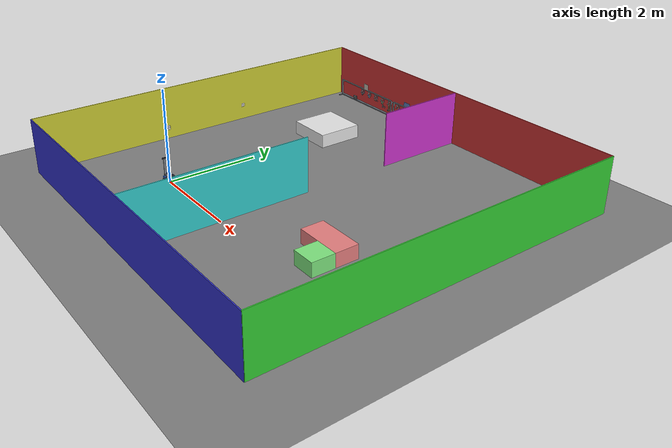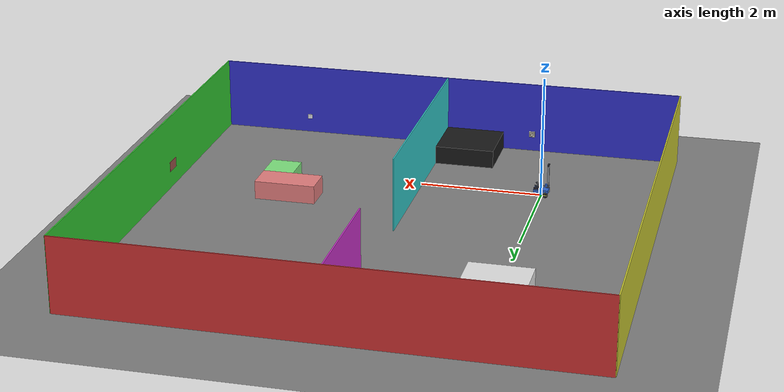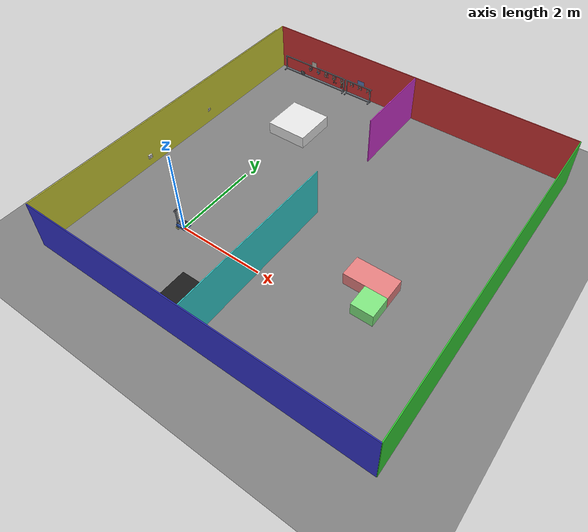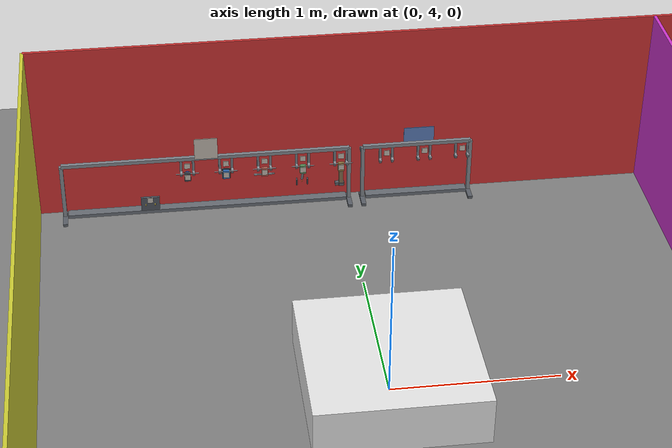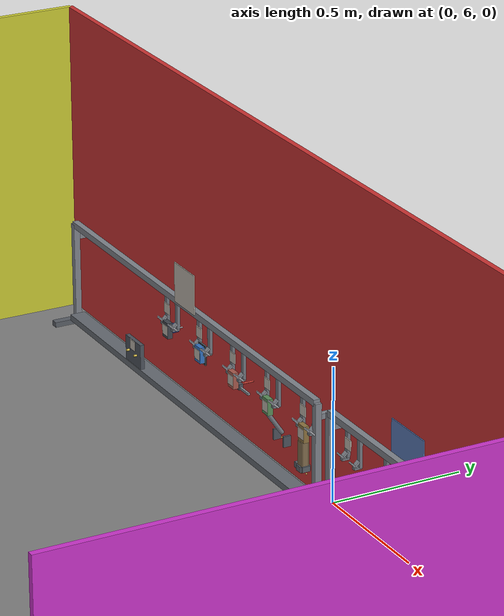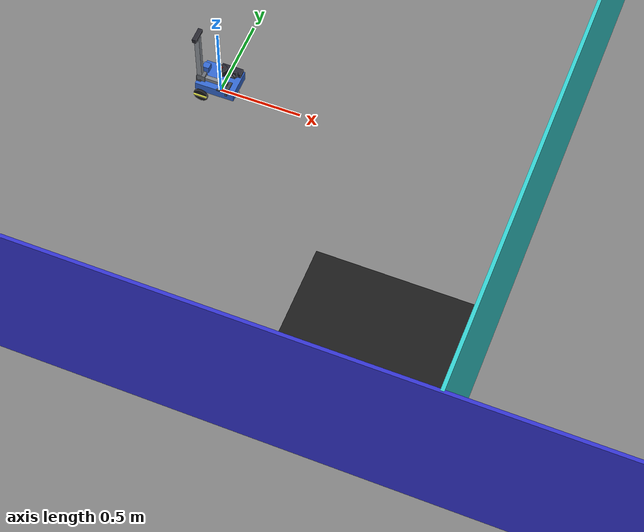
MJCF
<mujoco>
  <include file="world_fork.xml"/>

  <worldbody>
    <geom name="floor" type="plane" size="10 10 0.1" rgba="0.5 0.5 0.5 1"/>
  </worldbody>
  <include file="room_1_scenery.xml"/>
  <include file="hub_rack.xml"/>
</mujoco>

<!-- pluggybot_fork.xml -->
<mujocoinclude>
  <visual>
    <global offwidth="1280" offheight="720"/>
    <quality offsamples="0"/>
  </visual>

  <worldbody>

    <!-- origin at axle height (aka wheel radius) -->
    <body name="pluggybot" pos="0 0 0.045">
      <freejoint />

      <!-- For the gyroscope  -->
      <site name="imu" pos="0 0 0.05"/>

      <geom
        name="chassis"
        type="box"
        size="0.12 0.09 0.03"
        pos="0 0 0.045"
        mass="0.9"
        rgba="0.2 0.4 0.8 1"
      />

      <geom
        name="battery"
        type="box"
        size="0.065 0.023 0.013"
        pos="0.05 0.06 0.092"
        mass="0.40"
        rgba="0.15 0.15 0.2 1"
      />

      <!--  Head  -->
      <body name="head" pos="-0.08 0 0.135">
        <geom
          name="head_mount"
          type="box"
          size="0.02 0.02 0.02"
          pos="0 0 0"
          mass="0.12"
          rgba="0.2 0.4 0.8 1"
        />

        <!--  Cameras  -->
        <!--  Decoding xyaxes="0 -1 0  0 0 1":
                image-right is body −y, image-up is body +z,
                which forces the viewing direction to be body +x
        -->
        <camera name="left_eye" pos="0.03 0.03 0" xyaxes="0 -1 0 0 0 1" fovy="41"/>

      </body>

      <geom name="lidar_body" type="cylinder" size="0.028 0.022"
            pos="0.02 0 0.150" mass="0.11" rgba="0.15 0.15 0.18 1"/>
      <site name="lidar" pos="0.02 0 0.178" size="0.004"
            rgba="0.9 0.2 0.2 1"/>

      <body name="left_wheel" pos="-0.08 0.105 0">
        <joint
          name="left_wheel_joint"
          type="hinge"
          axis="0 1 0"
          armature="0.012"
          damping="0.05"
          frictionloss="0.05"
        />
        <geom
          name="left_tire"
          type="cylinder"
          size="0.045 0.005"
          zaxis="0 1 0"
          mass="0.05"
          rgba="0.1 0.1 0.1 1"
        />
        <!-- Spoke - purely visual, to see rotation  -->
        <geom
          type="box"
          size="0.04 0.013 0.004"
          mass="0.001"
          contype="0"
          conaffinity="0"
          rgba="1 1 0.3 1"
        />
      </body>

      <body name="right_wheel" pos="-0.08 -0.105 0">
        <joint
          name="right_wheel_joint"
          type="hinge"
          axis="0 1 0"
          armature="0.012"
          damping="0.05"
          frictionloss="0.05"
        />
        <!-- frictionloss: the parking brake -- see left_wheel_joint. -->
        <geom
          name="right_tire"
          type="cylinder"
          size="0.045 0.005"
          zaxis="0 1 0"
          mass="0.05"
          rgba="0.1 0.1 0.1 1"
        />
        <!-- Spoke - purely visual, to see rotation  -->
        <geom
          type="box"
          size="0.04 0.013 0.004"
          mass="0.001"
          contype="0"
          conaffinity="0"
          rgba="1 1 0.3 1"
        />
      </body>

      <geom
        name="caster"
        type="sphere"
        size="0.02"
        pos="0.10 0 -0.025"
        mass="0.02"
        condim="1"
        priority="1"
      />

      <!-- Mast: fixed column + lift motor block at its foot (igus NEMA11
           lead-screw class). Column top at body-local z=0.455. TBD masses. -->
      <geom name="mast" type="box" size="0.015 0.015 0.19"
            pos="-0.10 -0.05 0.265" mass="0.20" rgba="0.55 0.57 0.6 1"/>
      <geom name="lift_motor" type="box" size="0.015 0.02 0.02"
            pos="-0.105 -0.05 0.095" mass="0.15" rgba="0.3 0.3 0.32 1"/>

      <geom name="depth_cam_body" type="box" size="0.0125 0.045 0.0125"
            pos="-0.10 -0.05 0.4675" mass="0.072" rgba="0.15 0.15 0.18 1"/>
      <camera name="depth_eye" pos="-0.086 -0.05 0.4675"
              xyaxes="0 -1 0  0.6428 0 0.7660" fovy="58"/>

      <body name="carriage" pos="-0.10 -0.05 0.10">
        <joint name="lift_joint" type="slide" axis="0 0 1" range="0 0.31"
               damping="10"/>
        <geom name="carriage_block" type="box" size="0.025 0.02 0.022"
              pos="0.01 0 0.008" mass="0.25" rgba="0.4 0.42 0.45 1"/>

        <camera name="dock_eye" pos="0.03 0 0.06" xyaxes="0 -1 0 0 0 1" fovy="41"/>

        <!-- Telescoping arm: short tube, 0.20 m stroke. Retracted, the plug
             tip sits at body-local +0.059 — safely behind the +0.12 bumper. -->
        <body name="arm" pos="0 0 0">
          <joint name="arm_joint" type="slide" axis="1 0 0" range="0 0.20"
                 damping="5"/>
          <geom name="arm_tube" type="box" size="0.06 0.012 0.012"
                pos="0.08 0 0" mass="0.12" rgba="0.5 0.52 0.55 1"/>

          <body name="tool_fork" pos="0.14 0 0.019" euler="0 0 180">
            <joint name="fork_lat_y" type="slide" axis="0 1 0" range="-0.02 0.02"
                   stiffness="150" damping="4" armature="1e-5"/>
            <joint name="fork_lat_z" type="slide" axis="0 0 1" range="-0.02 0.02"
                   stiffness="150" damping="4" armature="1e-5"/>
            <joint name="fork_rot_z" type="hinge" axis="0 0 1" range="-0.35 0.35"
                   stiffness="1.0" damping="0.05" armature="1e-5"/>
            <joint name="fork_rot_y" type="hinge" axis="0 1 0" range="-0.35 0.35"
                   stiffness="1.0" damping="0.05" armature="1e-5"/>
            <geom name="fork_bridge" type="box" size="0.006 0.064 0.005"
                  pos="-0.014 0 -0.010" mass="0.020" rgba="0.30 0.32 0.36 1"/>
            <geom name="fork_prong_l" type="box" size="0.035 0.005 0.004"
                  pos="-0.020 0.058 -0.014" mass="0.008" rgba="0.30 0.32 0.36 1"/>
            <geom name="fork_prong_r" type="box" size="0.035 0.005 0.004"
                  pos="-0.020 -0.058 -0.014" mass="0.008" rgba="0.30 0.32 0.36 1"/>
            <geom name="fork_vl_a" type="box" size="0.011 0.006 0.003"
                  pos="-0.0628 0.058 0.0018" euler="0 45 0" mass="0.002"
                  rgba="0.30 0.32 0.36 1"/>
            <geom name="fork_vl_b" type="box" size="0.011 0.006 0.003"
                  pos="-0.0472 0.058 0.0018" euler="0 -45 0" mass="0.002"
                  rgba="0.30 0.32 0.36 1"/>
            <geom name="fork_vr_a" type="box" size="0.011 0.006 0.003"
                  pos="-0.0628 -0.058 0.0018" euler="0 45 0" mass="0.002"
                  rgba="0.30 0.32 0.36 1"/>
            <geom name="fork_vr_b" type="box" size="0.011 0.006 0.003"
                  pos="-0.0472 -0.058 0.0018" euler="0 -45 0" mass="0.002"
                  rgba="0.30 0.32 0.36 1"/>
            <geom name="fork_stop_l" type="box" size="0.006 0.004 0.012"
                  pos="-0.055 0.079 -0.002" mass="0.004" rgba="0.30 0.32 0.36 1"/>
            <geom name="fork_stop_r" type="box" size="0.006 0.004 0.012"
                  pos="-0.055 -0.079 -0.002" mass="0.004" rgba="0.30 0.32 0.36 1"/>
                 Depth is bounded by the PARKED envelope, not by what the
                 lever would like. Arm retracted, the fork tucks over the
                 chassis, and there is only ~60 mm between the chassis top
                 (0.12) and the scanner's centre row (0.18) -- a first
                 version reaching to z=-0.056 sat its bracket ON the chassis
                 and jacked the whole fork up into the scan row. So the pad
                 stops at z=-0.036 (a ~29 mm lever below the peg) and the
                 bracket routes BEHIND the module rather than under it.

                 29 mm is also near the floor of what works, for a reason
                 worth writing down: the pad force is (tool torque / lever),
                 and it is reacted at the peg, which sits in a 45-degree V.
                 Push the peg horizontally harder than its own weight
                 (1.28 N) and it rides up the flank and out. At a 29 mm
                 lever that caps tool force around 1.5 N -- comfortably past
                 a marker's 0.5-1 N, but this is the number that shrinks if
                 the pad is moved up. -->
            <geom name="lean_pad" type="box" size="0.010 0.028 0.005"
                  pos="-0.0385 0 -0.031" mass="0.012"
                  rgba="0.24 0.26 0.30 1"/>
            <geom name="lean_pad_post" type="box" size="0.007 0.008 0.016"
                  pos="-0.023 0 -0.021" mass="0.008"
                  rgba="0.30 0.32 0.36 1"/>
            <site name="fork_vertex" pos="-0.055 0 -0.006" size="0.002"/>
          </body>
        </body>
      </body>

    </body>
  </worldbody>

  <!-- The arm tube passes beside the mast on a carriage bracket in the real
       igus unit; as primitives on one axis they would interpenetrate. -->
  <contact>
    <exclude body1="pluggybot" body2="arm"/>
  </contact>

  <actuator>
    <velocity
      name="left_motor"
      joint="left_wheel_joint"
      kv="0.5"
      ctrlrange="-21 21"
      forcerange="-2.06 2.06"
    />
    <velocity
      name="right_motor"
      joint="right_wheel_joint"
      kv="0.5"
      ctrlrange="-21 21"
      forcerange="-2.06 2.06"
    />
    <!-- Lift + arm: position servos (a stepper lead-screw IS a position
         device). forcerange from the igus DLE-LA-0001 spec: 50 N thrust.
         ctrl is the joint target in meters. -->
    <position
      name="lift"
      joint="lift_joint"
      kp="1200"
      kv="60"
      ctrlrange="0 0.31"
      forcerange="-50 50"
    />
    <position
      name="arm"
      joint="arm_joint"
      kp="1200"
      kv="60"
      ctrlrange="0 0.20"
      forcerange="-50 50"
    />
  </actuator>

  <sensor>
    <gyro name="imu_gyro" site="imu"/>
  </sensor>

</mujocoinclude>

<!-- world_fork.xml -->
<mujoco>
  <option integrator="implicitfast"/>

  <include file="pluggybot_fork.xml" />

  <worldbody>
    <light pos="0 0 3" dir="0 0 -1"/>
  </worldbody>
</mujoco>

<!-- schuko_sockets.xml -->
<mujocoinclude>
  <body name="socket_a" pos="-1.9530 1.0000 0.2600" euler="0 0 0.0">
      <geom name="socket_a_wall0" type="box" size="0.00850 0.00200 0.00723" pos="-0.00850 0.02050 0.00000" euler="0.00 0 0.00" rgba="0.5 0.5 0.5 0" solref="0.005 1" friction="0.3"/>
      <geom name="socket_a_wall1" type="box" size="0.00850 0.00200 0.00723" pos="-0.00850 0.01775 0.01025" euler="30.00 0 0.00" rgba="0.5 0.5 0.5 0" solref="0.005 1" friction="0.3"/>
      <geom name="socket_a_wall2" type="box" size="0.00850 0.00200 0.00723" pos="-0.00850 0.01025 0.01775" euler="60.00 0 0.00" rgba="0.5 0.5 0.5 0" solref="0.005 1" friction="0.3"/>
      <geom name="socket_a_wall3" type="box" size="0.00850 0.00200 0.00723" pos="-0.00850 0.00000 0.02050" euler="90.00 0 0.00" rgba="0.5 0.5 0.5 0" solref="0.005 1" friction="0.3"/>
      <geom name="socket_a_wall4" type="box" size="0.00850 0.00200 0.00723" pos="-0.00850 -0.01025 0.01775" euler="120.00 0 0.00" rgba="0.5 0.5 0.5 0" solref="0.005 1" friction="0.3"/>
      <geom name="socket_a_wall5" type="box" size="0.00850 0.00200 0.00723" pos="-0.00850 -0.01775 0.01025" euler="150.00 0 0.00" rgba="0.5 0.5 0.5 0" solref="0.005 1" friction="0.3"/>
      <geom name="socket_a_wall6" type="box" size="0.00850 0.00200 0.00723" pos="-0.00850 -0.02050 0.00000" euler="180.00 0 0.00" rgba="0.5 0.5 0.5 0" solref="0.005 1" friction="0.3"/>
      <geom name="socket_a_wall7" type="box" size="0.00850 0.00200 0.00723" pos="-0.00850 -0.01775 -0.01025" euler="210.00 0 0.00" rgba="0.5 0.5 0.5 0" solref="0.005 1" friction="0.3"/>
      <geom name="socket_a_wall8" type="box" size="0.00850 0.00200 0.00723" pos="-0.00850 -0.01025 -0.01775" euler="240.00 0 0.00" rgba="0.5 0.5 0.5 0" solref="0.005 1" friction="0.3"/>
      <geom name="socket_a_wall9" type="box" size="0.00850 0.00200 0.00723" pos="-0.00850 -0.00000 -0.02050" euler="270.00 0 0.00" rgba="0.5 0.5 0.5 0" solref="0.005 1" friction="0.3"/>
      <geom name="socket_a_wall10" type="box" size="0.00850 0.00200 0.00723" pos="-0.00850 0.01025 -0.01775" euler="300.00 0 0.00" rgba="0.5 0.5 0.5 0" solref="0.005 1" friction="0.3"/>
      <geom name="socket_a_wall11" type="box" size="0.00850 0.00200 0.00723" pos="-0.00850 0.01775 -0.01025" euler="330.00 0 0.00" rgba="0.5 0.5 0.5 0" solref="0.005 1" friction="0.3"/>
      <geom name="socket_a_funnel0" type="box" size="0.00141 0.00200 0.00659" pos="0.00100 0.02150 0.00000" euler="0.00 0 45.00" rgba="0.5 0.5 0.5 0" solref="0.005 1" friction="0.3"/>
      <geom name="socket_a_funnel1" type="box" size="0.00141 0.00200 0.00659" pos="0.00100 0.01862 0.01075" euler="30.00 0 45.00" rgba="0.5 0.5 0.5 0" solref="0.005 1" friction="0.3"/>
      <geom name="socket_a_funnel2" type="box" size="0.00141 0.00200 0.00659" pos="0.00100 0.01075 0.01862" euler="60.00 0 45.00" rgba="0.5 0.5 0.5 0" solref="0.005 1" friction="0.3"/>
      <geom name="socket_a_funnel3" type="box" size="0.00141 0.00200 0.00659" pos="0.00100 0.00000 0.02150" euler="90.00 0 45.00" rgba="0.5 0.5 0.5 0" solref="0.005 1" friction="0.3"/>
      <geom name="socket_a_funnel4" type="box" size="0.00141 0.00200 0.00659" pos="0.00100 -0.01075 0.01862" euler="120.00 0 45.00" rgba="0.5 0.5 0.5 0" solref="0.005 1" friction="0.3"/>
      <geom name="socket_a_funnel5" type="box" size="0.00141 0.00200 0.00659" pos="0.00100 -0.01862 0.01075" euler="150.00 0 45.00" rgba="0.5 0.5 0.5 0" solref="0.005 1" friction="0.3"/>
      <geom name="socket_a_funnel6" type="box" size="0.00141 0.00200 0.00659" pos="0.00100 -0.02150 0.00000" euler="180.00 0 45.00" rgba="0.5 0.5 0.5 0" solref="0.005 1" friction="0.3"/>
      <geom name="socket_a_funnel7" type="box" size="0.00141 0.00200 0.00659" pos="0.00100 -0.01862 -0.01075" euler="210.00 0 45.00" rgba="0.5 0.5 0.5 0" solref="0.005 1" friction="0.3"/>
      <geom name="socket_a_funnel8" type="box" size="0.00141 0.00200 0.00659" pos="0.00100 -0.01075 -0.01862" euler="240.00 0 45.00" rgba="0.5 0.5 0.5 0" solref="0.005 1" friction="0.3"/>
      <geom name="socket_a_funnel9" type="box" size="0.00141 0.00200 0.00659" pos="0.00100 -0.00000 -0.02150" euler="270.00 0 45.00" rgba="0.5 0.5 0.5 0" solref="0.005 1" friction="0.3"/>
      <geom name="socket_a_funnel10" type="box" size="0.00141 0.00200 0.00659" pos="0.00100 0.01075 -0.01862" euler="300.00 0 45.00" rgba="0.5 0.5 0.5 0" solref="0.005 1" friction="0.3"/>
      <geom name="socket_a_funnel11" type="box" size="0.00141 0.00200 0.00659" pos="0.00100 0.01862 -0.01075" euler="330.00 0 45.00" rgba="0.5 0.5 0.5 0" solref="0.005 1" friction="0.3"/>
      <geom name="socket_a_floor_top" type="box" size="0.01 0.03 0.01360"
            pos="-0.02700 0 0.01640" rgba="0.5 0.5 0.5 0" solref="0.005 1" friction="0.3"/>
      <geom name="socket_a_floor_bot" type="box" size="0.01 0.03 0.01360"
            pos="-0.02700 0 -0.01640" rgba="0.5 0.5 0.5 0" solref="0.005 1" friction="0.3"/>
      <geom name="socket_a_floor_mid" type="box" size="0.01 0.00670 0.00280"
            pos="-0.02700 0 0" rgba="0.5 0.5 0.5 0" solref="0.005 1" friction="0.3"/>
      <geom name="socket_a_floor_l" type="box" size="0.01 0.00885 0.00280"
            pos="-0.02700 0.02115 0" rgba="0.5 0.5 0.5 0" solref="0.005 1" friction="0.3"/>
      <geom name="socket_a_floor_r" type="box" size="0.01 0.00885 0.00280"
            pos="-0.02700 -0.02115 0" rgba="0.5 0.5 0.5 0" solref="0.005 1" friction="0.3"/>
      <geom name="socket_a_plate_t" type="box" size="0.001 0.055 0.01675"
            pos="0.00300 0 0.03825" rgba="0.5 0.5 0.5 0" solref="0.005 1" friction="0.3"/>
      <geom name="socket_a_plate_b" type="box" size="0.001 0.055 0.01675"
            pos="0.00300 0 -0.03825" rgba="0.5 0.5 0.5 0" solref="0.005 1" friction="0.3"/>
      <geom name="socket_a_plate_l" type="box" size="0.001 0.01675 0.02150"
            pos="0.00300 0.03825 0" rgba="0.5 0.5 0.5 0" solref="0.005 1" friction="0.3"/>
      <geom name="socket_a_plate_r" type="box" size="0.001 0.01675 0.02150"
            pos="0.00300 -0.03825 0" rgba="0.5 0.5 0.5 0" solref="0.005 1" friction="0.3"/>
  </body>
  <body name="socket_b" pos="0.5000 -1.9530 0.3000" euler="0 0 90.0">
      <geom name="socket_b_wall0" type="box" size="0.00850 0.00200 0.00723" pos="-0.00850 0.02050 0.00000" euler="0.00 0 0.00" rgba="0.5 0.5 0.5 0" solref="0.005 1" friction="0.3"/>
      <geom name="socket_b_wall1" type="box" size="0.00850 0.00200 0.00723" pos="-0.00850 0.01775 0.01025" euler="30.00 0 0.00" rgba="0.5 0.5 0.5 0" solref="0.005 1" friction="0.3"/>
      <geom name="socket_b_wall2" type="box" size="0.00850 0.00200 0.00723" pos="-0.00850 0.01025 0.01775" euler="60.00 0 0.00" rgba="0.5 0.5 0.5 0" solref="0.005 1" friction="0.3"/>
      <geom name="socket_b_wall3" type="box" size="0.00850 0.00200 0.00723" pos="-0.00850 0.00000 0.02050" euler="90.00 0 0.00" rgba="0.5 0.5 0.5 0" solref="0.005 1" friction="0.3"/>
      <geom name="socket_b_wall4" type="box" size="0.00850 0.00200 0.00723" pos="-0.00850 -0.01025 0.01775" euler="120.00 0 0.00" rgba="0.5 0.5 0.5 0" solref="0.005 1" friction="0.3"/>
      <geom name="socket_b_wall5" type="box" size="0.00850 0.00200 0.00723" pos="-0.00850 -0.01775 0.01025" euler="150.00 0 0.00" rgba="0.5 0.5 0.5 0" solref="0.005 1" friction="0.3"/>
      <geom name="socket_b_wall6" type="box" size="0.00850 0.00200 0.00723" pos="-0.00850 -0.02050 0.00000" euler="180.00 0 0.00" rgba="0.5 0.5 0.5 0" solref="0.005 1" friction="0.3"/>
      <geom name="socket_b_wall7" type="box" size="0.00850 0.00200 0.00723" pos="-0.00850 -0.01775 -0.01025" euler="210.00 0 0.00" rgba="0.5 0.5 0.5 0" solref="0.005 1" friction="0.3"/>
      <geom name="socket_b_wall8" type="box" size="0.00850 0.00200 0.00723" pos="-0.00850 -0.01025 -0.01775" euler="240.00 0 0.00" rgba="0.5 0.5 0.5 0" solref="0.005 1" friction="0.3"/>
      <geom name="socket_b_wall9" type="box" size="0.00850 0.00200 0.00723" pos="-0.00850 -0.00000 -0.02050" euler="270.00 0 0.00" rgba="0.5 0.5 0.5 0" solref="0.005 1" friction="0.3"/>
      <geom name="socket_b_wall10" type="box" size="0.00850 0.00200 0.00723" pos="-0.00850 0.01025 -0.01775" euler="300.00 0 0.00" rgba="0.5 0.5 0.5 0" solref="0.005 1" friction="0.3"/>
      <geom name="socket_b_wall11" type="box" size="0.00850 0.00200 0.00723" pos="-0.00850 0.01775 -0.01025" euler="330.00 0 0.00" rgba="0.5 0.5 0.5 0" solref="0.005 1" friction="0.3"/>
      <geom name="socket_b_funnel0" type="box" size="0.00141 0.00200 0.00659" pos="0.00100 0.02150 0.00000" euler="0.00 0 45.00" rgba="0.5 0.5 0.5 0" solref="0.005 1" friction="0.3"/>
      <geom name="socket_b_funnel1" type="box" size="0.00141 0.00200 0.00659" pos="0.00100 0.01862 0.01075" euler="30.00 0 45.00" rgba="0.5 0.5 0.5 0" solref="0.005 1" friction="0.3"/>
      <geom name="socket_b_funnel2" type="box" size="0.00141 0.00200 0.00659" pos="0.00100 0.01075 0.01862" euler="60.00 0 45.00" rgba="0.5 0.5 0.5 0" solref="0.005 1" friction="0.3"/>
      <geom name="socket_b_funnel3" type="box" size="0.00141 0.00200 0.00659" pos="0.00100 0.00000 0.02150" euler="90.00 0 45.00" rgba="0.5 0.5 0.5 0" solref="0.005 1" friction="0.3"/>
      <geom name="socket_b_funnel4" type="box" size="0.00141 0.00200 0.00659" pos="0.00100 -0.01075 0.01862" euler="120.00 0 45.00" rgba="0.5 0.5 0.5 0" solref="0.005 1" friction="0.3"/>
      <geom name="socket_b_funnel5" type="box" size="0.00141 0.00200 0.00659" pos="0.00100 -0.01862 0.01075" euler="150.00 0 45.00" rgba="0.5 0.5 0.5 0" solref="0.005 1" friction="0.3"/>
      <geom name="socket_b_funnel6" type="box" size="0.00141 0.00200 0.00659" pos="0.00100 -0.02150 0.00000" euler="180.00 0 45.00" rgba="0.5 0.5 0.5 0" solref="0.005 1" friction="0.3"/>
      <geom name="socket_b_funnel7" type="box" size="0.00141 0.00200 0.00659" pos="0.00100 -0.01862 -0.01075" euler="210.00 0 45.00" rgba="0.5 0.5 0.5 0" solref="0.005 1" friction="0.3"/>
      <geom name="socket_b_funnel8" type="box" size="0.00141 0.00200 0.00659" pos="0.00100 -0.01075 -0.01862" euler="240.00 0 45.00" rgba="0.5 0.5 0.5 0" solref="0.005 1" friction="0.3"/>
      <geom name="socket_b_funnel9" type="box" size="0.00141 0.00200 0.00659" pos="0.00100 -0.00000 -0.02150" euler="270.00 0 45.00" rgba="0.5 0.5 0.5 0" solref="0.005 1" friction="0.3"/>
      <geom name="socket_b_funnel10" type="box" size="0.00141 0.00200 0.00659" pos="0.00100 0.01075 -0.01862" euler="300.00 0 45.00" rgba="0.5 0.5 0.5 0" solref="0.005 1" friction="0.3"/>
      <geom name="socket_b_funnel11" type="box" size="0.00141 0.00200 0.00659" pos="0.00100 0.01862 -0.01075" euler="330.00 0 45.00" rgba="0.5 0.5 0.5 0" solref="0.005 1" friction="0.3"/>
      <geom name="socket_b_floor_top" type="box" size="0.01 0.03 0.01360"
            pos="-0.02700 0 0.01640" rgba="0.5 0.5 0.5 0" solref="0.005 1" friction="0.3"/>
      <geom name="socket_b_floor_bot" type="box" size="0.01 0.03 0.01360"
            pos="-0.02700 0 -0.01640" rgba="0.5 0.5 0.5 0" solref="0.005 1" friction="0.3"/>
      <geom name="socket_b_floor_mid" type="box" size="0.01 0.00670 0.00280"
            pos="-0.02700 0 0" rgba="0.5 0.5 0.5 0" solref="0.005 1" friction="0.3"/>
      <geom name="socket_b_floor_l" type="box" size="0.01 0.00885 0.00280"
            pos="-0.02700 0.02115 0" rgba="0.5 0.5 0.5 0" solref="0.005 1" friction="0.3"/>
      <geom name="socket_b_floor_r" type="box" size="0.01 0.00885 0.00280"
            pos="-0.02700 -0.02115 0" rgba="0.5 0.5 0.5 0" solref="0.005 1" friction="0.3"/>
      <geom name="socket_b_plate_t" type="box" size="0.001 0.055 0.01675"
            pos="0.00300 0 0.03825" rgba="0.5 0.5 0.5 0" solref="0.005 1" friction="0.3"/>
      <geom name="socket_b_plate_b" type="box" size="0.001 0.055 0.01675"
            pos="0.00300 0 -0.03825" rgba="0.5 0.5 0.5 0" solref="0.005 1" friction="0.3"/>
      <geom name="socket_b_plate_l" type="box" size="0.001 0.01675 0.02150"
            pos="0.00300 0.03825 0" rgba="0.5 0.5 0.5 0" solref="0.005 1" friction="0.3"/>
      <geom name="socket_b_plate_r" type="box" size="0.001 0.01675 0.02150"
            pos="0.00300 -0.03825 0" rgba="0.5 0.5 0.5 0" solref="0.005 1" friction="0.3"/>
  </body>
  <body name="socket_c" pos="5.9530 4.5000 0.3800" euler="0 0 180.0">
      <geom name="socket_c_wall0" type="box" size="0.00850 0.00200 0.00723" pos="-0.00850 0.02050 0.00000" euler="0.00 0 0.00" rgba="0.5 0.5 0.5 0" solref="0.005 1" friction="0.3"/>
      <geom name="socket_c_wall1" type="box" size="0.00850 0.00200 0.00723" pos="-0.00850 0.01775 0.01025" euler="30.00 0 0.00" rgba="0.5 0.5 0.5 0" solref="0.005 1" friction="0.3"/>
      <geom name="socket_c_wall2" type="box" size="0.00850 0.00200 0.00723" pos="-0.00850 0.01025 0.01775" euler="60.00 0 0.00" rgba="0.5 0.5 0.5 0" solref="0.005 1" friction="0.3"/>
      <geom name="socket_c_wall3" type="box" size="0.00850 0.00200 0.00723" pos="-0.00850 0.00000 0.02050" euler="90.00 0 0.00" rgba="0.5 0.5 0.5 0" solref="0.005 1" friction="0.3"/>
      <geom name="socket_c_wall4" type="box" size="0.00850 0.00200 0.00723" pos="-0.00850 -0.01025 0.01775" euler="120.00 0 0.00" rgba="0.5 0.5 0.5 0" solref="0.005 1" friction="0.3"/>
      <geom name="socket_c_wall5" type="box" size="0.00850 0.00200 0.00723" pos="-0.00850 -0.01775 0.01025" euler="150.00 0 0.00" rgba="0.5 0.5 0.5 0" solref="0.005 1" friction="0.3"/>
      <geom name="socket_c_wall6" type="box" size="0.00850 0.00200 0.00723" pos="-0.00850 -0.02050 0.00000" euler="180.00 0 0.00" rgba="0.5 0.5 0.5 0" solref="0.005 1" friction="0.3"/>
      <geom name="socket_c_wall7" type="box" size="0.00850 0.00200 0.00723" pos="-0.00850 -0.01775 -0.01025" euler="210.00 0 0.00" rgba="0.5 0.5 0.5 0" solref="0.005 1" friction="0.3"/>
      <geom name="socket_c_wall8" type="box" size="0.00850 0.00200 0.00723" pos="-0.00850 -0.01025 -0.01775" euler="240.00 0 0.00" rgba="0.5 0.5 0.5 0" solref="0.005 1" friction="0.3"/>
      <geom name="socket_c_wall9" type="box" size="0.00850 0.00200 0.00723" pos="-0.00850 -0.00000 -0.02050" euler="270.00 0 0.00" rgba="0.5 0.5 0.5 0" solref="0.005 1" friction="0.3"/>
      <geom name="socket_c_wall10" type="box" size="0.00850 0.00200 0.00723" pos="-0.00850 0.01025 -0.01775" euler="300.00 0 0.00" rgba="0.5 0.5 0.5 0" solref="0.005 1" friction="0.3"/>
      <geom name="socket_c_wall11" type="box" size="0.00850 0.00200 0.00723" pos="-0.00850 0.01775 -0.01025" euler="330.00 0 0.00" rgba="0.5 0.5 0.5 0" solref="0.005 1" friction="0.3"/>
      <geom name="socket_c_funnel0" type="box" size="0.00141 0.00200 0.00659" pos="0.00100 0.02150 0.00000" euler="0.00 0 45.00" rgba="0.5 0.5 0.5 0" solref="0.005 1" friction="0.3"/>
      <geom name="socket_c_funnel1" type="box" size="0.00141 0.00200 0.00659" pos="0.00100 0.01862 0.01075" euler="30.00 0 45.00" rgba="0.5 0.5 0.5 0" solref="0.005 1" friction="0.3"/>
      <geom name="socket_c_funnel2" type="box" size="0.00141 0.00200 0.00659" pos="0.00100 0.01075 0.01862" euler="60.00 0 45.00" rgba="0.5 0.5 0.5 0" solref="0.005 1" friction="0.3"/>
      <geom name="socket_c_funnel3" type="box" size="0.00141 0.00200 0.00659" pos="0.00100 0.00000 0.02150" euler="90.00 0 45.00" rgba="0.5 0.5 0.5 0" solref="0.005 1" friction="0.3"/>
      <geom name="socket_c_funnel4" type="box" size="0.00141 0.00200 0.00659" pos="0.00100 -0.01075 0.01862" euler="120.00 0 45.00" rgba="0.5 0.5 0.5 0" solref="0.005 1" friction="0.3"/>
      <geom name="socket_c_funnel5" type="box" size="0.00141 0.00200 0.00659" pos="0.00100 -0.01862 0.01075" euler="150.00 0 45.00" rgba="0.5 0.5 0.5 0" solref="0.005 1" friction="0.3"/>
      <geom name="socket_c_funnel6" type="box" size="0.00141 0.00200 0.00659" pos="0.00100 -0.02150 0.00000" euler="180.00 0 45.00" rgba="0.5 0.5 0.5 0" solref="0.005 1" friction="0.3"/>
      <geom name="socket_c_funnel7" type="box" size="0.00141 0.00200 0.00659" pos="0.00100 -0.01862 -0.01075" euler="210.00 0 45.00" rgba="0.5 0.5 0.5 0" solref="0.005 1" friction="0.3"/>
      <geom name="socket_c_funnel8" type="box" size="0.00141 0.00200 0.00659" pos="0.00100 -0.01075 -0.01862" euler="240.00 0 45.00" rgba="0.5 0.5 0.5 0" solref="0.005 1" friction="0.3"/>
      <geom name="socket_c_funnel9" type="box" size="0.00141 0.00200 0.00659" pos="0.00100 -0.00000 -0.02150" euler="270.00 0 45.00" rgba="0.5 0.5 0.5 0" solref="0.005 1" friction="0.3"/>
      <geom name="socket_c_funnel10" type="box" size="0.00141 0.00200 0.00659" pos="0.00100 0.01075 -0.01862" euler="300.00 0 45.00" rgba="0.5 0.5 0.5 0" solref="0.005 1" friction="0.3"/>
      <geom name="socket_c_funnel11" type="box" size="0.00141 0.00200 0.00659" pos="0.00100 0.01862 -0.01075" euler="330.00 0 45.00" rgba="0.5 0.5 0.5 0" solref="0.005 1" friction="0.3"/>
      <geom name="socket_c_floor_top" type="box" size="0.01 0.03 0.01360"
            pos="-0.02700 0 0.01640" rgba="0.5 0.5 0.5 0" solref="0.005 1" friction="0.3"/>
      <geom name="socket_c_floor_bot" type="box" size="0.01 0.03 0.01360"
            pos="-0.02700 0 -0.01640" rgba="0.5 0.5 0.5 0" solref="0.005 1" friction="0.3"/>
      <geom name="socket_c_floor_mid" type="box" size="0.01 0.00670 0.00280"
            pos="-0.02700 0 0" rgba="0.5 0.5 0.5 0" solref="0.005 1" friction="0.3"/>
      <geom name="socket_c_floor_l" type="box" size="0.01 0.00885 0.00280"
            pos="-0.02700 0.02115 0" rgba="0.5 0.5 0.5 0" solref="0.005 1" friction="0.3"/>
      <geom name="socket_c_floor_r" type="box" size="0.01 0.00885 0.00280"
            pos="-0.02700 -0.02115 0" rgba="0.5 0.5 0.5 0" solref="0.005 1" friction="0.3"/>
      <geom name="socket_c_plate_t" type="box" size="0.001 0.055 0.01675"
            pos="0.00300 0 0.03825" rgba="0.5 0.5 0.5 0" solref="0.005 1" friction="0.3"/>
      <geom name="socket_c_plate_b" type="box" size="0.001 0.055 0.01675"
            pos="0.00300 0 -0.03825" rgba="0.5 0.5 0.5 0" solref="0.005 1" friction="0.3"/>
      <geom name="socket_c_plate_l" type="box" size="0.001 0.01675 0.02150"
            pos="0.00300 0.03825 0" rgba="0.5 0.5 0.5 0" solref="0.005 1" friction="0.3"/>
      <geom name="socket_c_plate_r" type="box" size="0.001 0.01675 0.02150"
            pos="0.00300 -0.03825 0" rgba="0.5 0.5 0.5 0" solref="0.005 1" friction="0.3"/>
  </body>
</mujocoinclude>

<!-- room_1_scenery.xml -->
<!-- room_1 SCENERY: the floor plan behind room_hub.xml -- walls, obstacles,
     and the plug era's outlets, decoys and socket include, kept as scenery
     until the rover's worlds go (#376 stage C). -->
<mujocoinclude>
  <worldbody>

    <!-- Light the whole area -->
    <light dir="0 0 -1" directional="true"/>

    <!--  Walls  -->

    <!-- Wall north (red)  -->
    <body name="wall-north" pos="2.0 6.0 0.6">
      <geom type="box" size="4.0 0.01 0.6" rgba="0.8 0.2 0.2 1"/>
    </body>

    <!-- Wall east (green) -->
    <body name="wall-east" pos="6.0 2.0 0.6">
      <geom type="box" size="0.01 4.0 0.6" rgba="0.2 0.8 0.2 1"/>
    </body>

    <!-- Wall south (blue)  -->
    <body name="wall-south" pos="2.0 -2.0 0.6">
      <geom type="box" size="4.0 0.01 0.6" rgba="0.2 0.2 0.8 1"/>
    </body>

    <!-- Wall west (yellow) -->
    <body name="wall-west" pos="-2.0 2.0 0.6">
      <geom type="box" size="0.01 4.0 0.6" rgba="0.8 0.8 0.2 1"/>
    </body>

    <!-- Wall divider top (purple) -->
    <body name="wall-divider-top" pos="2.0 5.0 0.6">
      <geom type="box" size="0.01 1.0 0.6" rgba="0.8 0.2 0.8 1"/>
    </body>

    <!-- Wall divider bottom (cyan) -->
    <body name="wall-divider-bottom" pos="2.0 0.0 0.6">
      <geom type="box" size="0.01 2.0 0.6" rgba="0.2 0.8 0.8 1"/>
    </body>

    <!--  Obstacles  -->

    <!-- Corner box (black) -->
    <body name="corner-box" pos="1.5 -1.5 0.15">
      <geom type="box" size="0.5 0.5 0.15" rgba="0.1 0.1 0.1 1"/>
    </body>

    <!-- Floor box (white) -->
    <body name="floor-box" pos="0.0 4 0.15">
      <geom type="box" size="0.5 0.5 0.15" rgba="0.9 0.9 0.9 1"/>
    </body>

    <!-- L box north (light red) -->
    <body name="L-box-north" pos="4.0 1 0.15">
      <geom type="box" size="0.5 0.25 0.15" rgba="0.9 0.5 0.5 1"/>
    </body>

    <!-- L box side (light green) -->
    <body name="L-box-side" pos="4.25 0.5 0.15">
      <geom type="box" size="0.25 0.25 0.15" rgba="0.5 0.9 0.5 1"/>
    </body>

    <!-- Dockable sockets: invisible collision geometry aligned with the
         visual outlets below (generated file — see header). -->
    <include file="schuko_sockets.xml"/>

    <!-- Outlet A: west wall, room 1. Bright white, slightly oversized plate. -->
    <body name="outlet_a" pos="-1.953 1.0 0.26" euler="0 0 0">
      <geom name="outlet_a_housing" type="box" size="0.0165 0.048 0.048"
            pos="-0.0205 0 0" rgba="0.91 0.90 0.87 1" contype="0" conaffinity="0"/>
      <geom name="outlet_a_plate" type="box" size="0.004 0.042 0.042"
            rgba="0.97 0.96 0.94 1" contype="0" conaffinity="0"/>
      <geom name="outlet_a_well" type="cylinder" size="0.028 0.0015" zaxis="1 0 0"
            pos="0.0045 0 0" rgba="0.78 0.77 0.74 1" contype="0" conaffinity="0"/>
      <geom name="outlet_a_wellfloor" type="cylinder" size="0.024 0.0015" zaxis="1 0 0"
            pos="0.0058 0 0" rgba="0.90 0.89 0.86 1" contype="0" conaffinity="0"/>
      <geom name="outlet_a_hole_l" type="cylinder" size="0.0024 0.0015" zaxis="1 0 0"
            pos="0.0068 0.0095 0" rgba="0.08 0.08 0.08 1" contype="0" conaffinity="0"/>
      <geom name="outlet_a_hole_r" type="cylinder" size="0.0024 0.0015" zaxis="1 0 0"
            pos="0.0068 -0.0095 0" rgba="0.08 0.08 0.08 1" contype="0" conaffinity="0"/>
      <geom name="outlet_a_clip_top" type="box" size="0.0018 0.005 0.0015"
            pos="0.0062 0 0.024" rgba="0.60 0.61 0.63 1" contype="0" conaffinity="0"/>
      <geom name="outlet_a_clip_bot" type="box" size="0.0018 0.005 0.0015"
            pos="0.0062 0 -0.024" rgba="0.60 0.61 0.63 1" contype="0" conaffinity="0"/>
    </body>

    <!-- Outlet B: south wall, room 1. Warm cream, slightly undersized plate. -->
    <body name="outlet_b" pos="0.5 -1.953 0.30" euler="0 0 90">
      <geom name="outlet_b_housing" type="box" size="0.0165 0.048 0.048"
            pos="-0.0205 0 0" rgba="0.91 0.90 0.87 1" contype="0" conaffinity="0"/>
      <geom name="outlet_b_plate" type="box" size="0.004 0.038 0.038"
            rgba="0.89 0.86 0.79 1" contype="0" conaffinity="0"/>
      <geom name="outlet_b_well" type="cylinder" size="0.028 0.0015" zaxis="1 0 0"
            pos="0.0045 0 0" rgba="0.70 0.68 0.62 1" contype="0" conaffinity="0"/>
      <geom name="outlet_b_wellfloor" type="cylinder" size="0.024 0.0015" zaxis="1 0 0"
            pos="0.0058 0 0" rgba="0.83 0.81 0.75 1" contype="0" conaffinity="0"/>
      <geom name="outlet_b_hole_l" type="cylinder" size="0.0024 0.0015" zaxis="1 0 0"
            pos="0.0068 0.0095 0" rgba="0.08 0.08 0.08 1" contype="0" conaffinity="0"/>
      <geom name="outlet_b_hole_r" type="cylinder" size="0.0024 0.0015" zaxis="1 0 0"
            pos="0.0068 -0.0095 0" rgba="0.08 0.08 0.08 1" contype="0" conaffinity="0"/>
      <geom name="outlet_b_clip_top" type="box" size="0.0018 0.005 0.0015"
            pos="0.0062 0 0.022" rgba="0.64 0.65 0.66 1" contype="0" conaffinity="0"/>
      <geom name="outlet_b_clip_bot" type="box" size="0.0018 0.005 0.0015"
            pos="0.0062 0 -0.022" rgba="0.64 0.65 0.66 1" contype="0" conaffinity="0"/>
    </body>

    <!-- Outlet C: east wall, room 2. Cool light gray, standard plate. -->
    <body name="outlet_c" pos="5.953 4.5 0.38" euler="0 0 180">
      <geom name="outlet_c_housing" type="box" size="0.0165 0.048 0.048"
            pos="-0.0205 0 0" rgba="0.91 0.90 0.87 1" contype="0" conaffinity="0"/>
      <geom name="outlet_c_plate" type="box" size="0.004 0.04 0.04"
            rgba="0.84 0.85 0.86 1" contype="0" conaffinity="0"/>
      <geom name="outlet_c_well" type="cylinder" size="0.028 0.0015" zaxis="1 0 0"
            pos="0.0045 0 0" rgba="0.66 0.67 0.69 1" contype="0" conaffinity="0"/>
      <geom name="outlet_c_wellfloor" type="cylinder" size="0.024 0.0015" zaxis="1 0 0"
            pos="0.0058 0 0" rgba="0.78 0.79 0.80 1" contype="0" conaffinity="0"/>
      <geom name="outlet_c_hole_l" type="cylinder" size="0.0024 0.0015" zaxis="1 0 0"
            pos="0.0068 0.0095 0" rgba="0.08 0.08 0.08 1" contype="0" conaffinity="0"/>
      <geom name="outlet_c_hole_r" type="cylinder" size="0.0024 0.0015" zaxis="1 0 0"
            pos="0.0068 -0.0095 0" rgba="0.08 0.08 0.08 1" contype="0" conaffinity="0"/>
      <geom name="outlet_c_clip_top" type="box" size="0.0018 0.005 0.0015"
            pos="0.0062 0 0.024" rgba="0.58 0.59 0.61 1" contype="0" conaffinity="0"/>
      <geom name="outlet_c_clip_bot" type="box" size="0.0018 0.005 0.0015"
            pos="0.0062 0 -0.024" rgba="0.58 0.59 0.61 1" contype="0" conaffinity="0"/>
    </body>

    <!--  Wall decoys: the plug era's hard negatives for its outlet
          detector, scenery now.  -->

    <!-- Light switch: west wall, room 1 (plate + rocker) -->
    <body name="decoy_switch_w" pos="-1.986 3.0 0.34" euler="0 0 0">
      <geom name="decoy_switch_w_plate" type="box" size="0.004 0.04 0.04"
            rgba="0.92 0.91 0.88 1" contype="0" conaffinity="0"/>
      <geom name="decoy_switch_w_rocker" type="box" size="0.004 0.018 0.026"
            pos="0.004 0 0" rgba="0.92 0.91 0.88 1" contype="0" conaffinity="0"/>
    </body>

    <!-- Blank plate: south wall, room 2 -->
    <body name="decoy_blank_s" pos="4.5 -1.986 0.28" euler="0 0 90">
      <geom name="decoy_blank_s_plate" type="box" size="0.004 0.04 0.04"
            rgba="0.88 0.88 0.90 1" contype="0" conaffinity="0"/>
    </body>

    <!-- Pictures: north wall room 1, east wall room 2 -->
    <body name="decoy_pic_n" pos="0.5 5.988 0.42" euler="0 0 270">
      <geom name="decoy_pic_n_canvas" type="box" size="0.002 0.10 0.06"
            rgba="0.35 0.48 0.72 1" contype="0" conaffinity="0"/>
    </body>
    <body name="decoy_pic_e" pos="5.988 1.0 0.36" euler="0 0 180">
      <geom name="decoy_pic_e_canvas" type="box" size="0.002 0.14 0.08"
            rgba="0.62 0.33 0.30 1" contype="0" conaffinity="0"/>
    </body>

  </worldbody>
</mujocoinclude>

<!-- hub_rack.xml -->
<mujocoinclude>
  <asset>
    <texture name="tagtex0" type="cube" file="tags/tag0.png"/>
    <material name="tagmat0" texture="tagtex0" specular="0.05" shininess="0.05" reflectance="0"/>
    <texture name="tagtex3" type="cube" file="tags/tag3.png"/>
    <material name="tagmat3" texture="tagtex3" specular="0.05" shininess="0.05" reflectance="0"/>
    <texture name="tagtex1" type="cube" file="tags/tag1.png"/>
    <material name="tagmat1" texture="tagtex1" specular="0.05" shininess="0.05" reflectance="0"/>
    <texture name="tagtex2" type="cube" file="tags/tag2.png"/>
    <material name="tagmat2" texture="tagtex2" specular="0.05" shininess="0.05" reflectance="0"/>
    <texture name="tagtex4" type="cube" file="tags/tag4.png"/>
    <material name="tagmat4" texture="tagtex4" specular="0.05" shininess="0.05" reflectance="0"/>
    <texture name="tagtex5" type="cube" file="tags/tag5.png"/>
    <material name="tagmat5" texture="tagtex5" specular="0.05" shininess="0.05" reflectance="0"/>
    <texture name="tagtex6" type="cube" file="tags/tag6.png"/>
    <material name="tagmat6" texture="tagtex6" specular="0.05" shininess="0.05" reflectance="0"/>
    <texture name="tagtex7" type="cube" file="tags/tag7.png"/>
    <material name="tagmat7" texture="tagtex7" specular="0.05" shininess="0.05" reflectance="0"/>
    <texture name="tagtex8" type="cube" file="tags/tag8.png"/>
    <material name="tagmat8" texture="tagtex8" specular="0.05" shininess="0.05" reflectance="0"/>
    <texture name="tagtex9" type="cube" file="tags/tag9.png"/>
    <material name="tagmat9" texture="tagtex9" specular="0.05" shininess="0.05" reflectance="0"/>
    <texture name="tagtex10" type="cube" file="tags/tag10.png"/>
    <material name="tagmat10" texture="tagtex10" specular="0.05" shininess="0.05" reflectance="0"/>
    <texture name="tagtex11" type="cube" file="tags/tag11.png"/>
    <material name="tagmat11" texture="tagtex11" specular="0.05" shininess="0.05" reflectance="0"/>
    <texture name="tagtex12" type="cube" file="tags/tag12.png"/>
    <material name="tagmat12" texture="tagtex12" specular="0.05" shininess="0.05" reflectance="0"/>
    <texture name="tagtex13" type="cube" file="tags/tag13.png"/>
    <material name="tagmat13" texture="tagtex13" specular="0.05" shininess="0.05" reflectance="0"/>
    <texture name="tagtex14" type="cube" file="tags/tag14.png"/>
    <material name="tagmat14" texture="tagtex14" specular="0.05" shininess="0.05" reflectance="0"/>
  </asset>
  <worldbody>
    <body name="rack" pos="-0.9000 5.9900 0.0000" euler="0 0 -90.0">
      <freejoint/>
      <geom name="rack_post_l" type="box" size="0.012 0.012 0.200"
            pos="0.0700 0.9300 0.200"
            mass="0.15" rgba="0.50 0.52 0.55 1"/>
      <geom name="rack_post_r" type="box" size="0.012 0.012 0.200"
            pos="0.0700 -0.9300 0.200"
            mass="0.15" rgba="0.50 0.52 0.55 1"/>
      <geom name="rack_rail" type="box" size="0.012 0.930 0.012"
            pos="0.0700 0 0.400" mass="0.20"
            rgba="0.50 0.52 0.55 1"/>
      <geom name="rack_foot_l" type="box" size="0.070 0.015 0.010"
            pos="0.10 0.9300 0.010" mass="0.10" friction="1.0"
            rgba="0.35 0.37 0.40 1"/>
      <geom name="rack_foot_r" type="box" size="0.070 0.015 0.010"
            pos="0.10 -0.9300 0.010" mass="0.10" friction="1.0"
            rgba="0.35 0.37 0.40 1"/>
      <geom name="rack_shelf" type="box" size="0.030 0.910 0.012"
            pos="0.08 0 0.032" mass="1.50" rgba="0.40 0.42 0.45 1"/>
      <geom name="rack_brace_l" type="box" size="0.0350 0.010 0.010"
            pos="0.0350 0.9300 0.35" mass="0.05"
            rgba="0.50 0.52 0.55 1"/>
      <geom name="rack_brace_r" type="box" size="0.0350 0.010 0.010"
            pos="0.0350 -0.9300 0.35" mass="0.05"
            rgba="0.50 0.52 0.55 1"/>
      <geom name="rack_tag" type="box"
            size="0.002 0.0750 0.0750"
            pos="0.0840 0 0.475"
            contype="0" conaffinity="0" material="tagmat0"/>
      <geom name="rack_tag_mast" type="box" size="0.006 0.006 0.045"
            pos="0.0700 0 0.445" mass="0.02"
            rgba="0.50 0.52 0.55 1"/>
            <geom name="baya_col_l" type="box" size="0.006 0.008 0.0585" pos="0.0700 0.1650 0.3415" rgba="0.45 0.47 0.50 1"/>
      <geom name="baya_foot_l" type="box" size="0.014 0.008 0.004" pos="0.0800 0.1650 0.284" rgba="0.45 0.47 0.50 1"/>
      <geom name="baya_tray_l_a" type="box" size="0.0110 0.0080 0.0030" pos="0.0822 0.1650 0.2998" euler="0 45 0" rgba="0.55 0.57 0.60 1"/>
      <geom name="baya_tray_l_b" type="box" size="0.0110 0.0080 0.0030" pos="0.0978 0.1650 0.2998" euler="0 -45 0" rgba="0.55 0.57 0.60 1"/>
      <geom name="baya_col_r" type="box" size="0.006 0.008 0.0585" pos="0.0700 0.0850 0.3415" rgba="0.45 0.47 0.50 1"/>
      <geom name="baya_foot_r" type="box" size="0.014 0.008 0.004" pos="0.0800 0.0850 0.284" rgba="0.45 0.47 0.50 1"/>
      <geom name="baya_tray_r_a" type="box" size="0.0110 0.0080 0.0030" pos="0.0822 0.0850 0.2998" euler="0 45 0" rgba="0.55 0.57 0.60 1"/>
      <geom name="baya_tray_r_b" type="box" size="0.0110 0.0080 0.0030" pos="0.0978 0.0850 0.2998" euler="0 -45 0" rgba="0.55 0.57 0.60 1"/>
      <geom name="baya_bay_tag" type="box" size="0.002 0.0187 0.0187" pos="0.0920 0.1250 0.3550" contype="0" conaffinity="0" material="tagmat1"/>
      <geom name="bayb_col_l" type="box" size="0.006 0.008 0.0585" pos="0.0700 -0.0850 0.3415" rgba="0.45 0.47 0.50 1"/>
      <geom name="bayb_foot_l" type="box" size="0.014 0.008 0.004" pos="0.0800 -0.0850 0.284" rgba="0.45 0.47 0.50 1"/>
      <geom name="bayb_tray_l_a" type="box" size="0.0110 0.0080 0.0030" pos="0.0822 -0.0850 0.2998" euler="0 45 0" rgba="0.55 0.57 0.60 1"/>
      <geom name="bayb_tray_l_b" type="box" size="0.0110 0.0080 0.0030" pos="0.0978 -0.0850 0.2998" euler="0 -45 0" rgba="0.55 0.57 0.60 1"/>
      <geom name="bayb_col_r" type="box" size="0.006 0.008 0.0585" pos="0.0700 -0.1650 0.3415" rgba="0.45 0.47 0.50 1"/>
      <geom name="bayb_foot_r" type="box" size="0.014 0.008 0.004" pos="0.0800 -0.1650 0.284" rgba="0.45 0.47 0.50 1"/>
      <geom name="bayb_tray_r_a" type="box" size="0.0110 0.0080 0.0030" pos="0.0822 -0.1650 0.2998" euler="0 45 0" rgba="0.55 0.57 0.60 1"/>
      <geom name="bayb_tray_r_b" type="box" size="0.0110 0.0080 0.0030" pos="0.0978 -0.1650 0.2998" euler="0 -45 0" rgba="0.55 0.57 0.60 1"/>
      <geom name="bayb_bay_tag" type="box" size="0.002 0.0187 0.0187" pos="0.0920 -0.1250 0.3550" contype="0" conaffinity="0" material="tagmat2"/>
      <geom name="bayc_col_l" type="box" size="0.006 0.008 0.0585" pos="0.0700 0.4150 0.3415" rgba="0.45 0.47 0.50 1"/>
      <geom name="bayc_foot_l" type="box" size="0.014 0.008 0.004" pos="0.0800 0.4150 0.284" rgba="0.45 0.47 0.50 1"/>
      <geom name="bayc_tray_l_a" type="box" size="0.0110 0.0080 0.0030" pos="0.0822 0.4150 0.2998" euler="0 45 0" rgba="0.55 0.57 0.60 1"/>
      <geom name="bayc_tray_l_b" type="box" size="0.0110 0.0080 0.0030" pos="0.0978 0.4150 0.2998" euler="0 -45 0" rgba="0.55 0.57 0.60 1"/>
      <geom name="bayc_col_r" type="box" size="0.006 0.008 0.0585" pos="0.0700 0.3350 0.3415" rgba="0.45 0.47 0.50 1"/>
      <geom name="bayc_foot_r" type="box" size="0.014 0.008 0.004" pos="0.0800 0.3350 0.284" rgba="0.45 0.47 0.50 1"/>
      <geom name="bayc_tray_r_a" type="box" size="0.0110 0.0080 0.0030" pos="0.0822 0.3350 0.2998" euler="0 45 0" rgba="0.55 0.57 0.60 1"/>
      <geom name="bayc_tray_r_b" type="box" size="0.0110 0.0080 0.0030" pos="0.0978 0.3350 0.2998" euler="0 -45 0" rgba="0.55 0.57 0.60 1"/>
      <geom name="bayc_bay_tag" type="box" size="0.002 0.0187 0.0187" pos="0.0920 0.3750 0.3550" contype="0" conaffinity="0" material="tagmat4"/>
      <geom name="bayd_col_l" type="box" size="0.006 0.008 0.0585" pos="0.0700 0.6650 0.3415" rgba="0.45 0.47 0.50 1"/>
      <geom name="bayd_foot_l" type="box" size="0.014 0.008 0.004" pos="0.0800 0.6650 0.284" rgba="0.45 0.47 0.50 1"/>
      <geom name="bayd_tray_l_a" type="box" size="0.0110 0.0080 0.0030" pos="0.0822 0.6650 0.2998" euler="0 45 0" rgba="0.55 0.57 0.60 1"/>
      <geom name="bayd_tray_l_b" type="box" size="0.0110 0.0080 0.0030" pos="0.0978 0.6650 0.2998" euler="0 -45 0" rgba="0.55 0.57 0.60 1"/>
      <geom name="bayd_col_r" type="box" size="0.006 0.008 0.0585" pos="0.0700 0.5850 0.3415" rgba="0.45 0.47 0.50 1"/>
      <geom name="bayd_foot_r" type="box" size="0.014 0.008 0.004" pos="0.0800 0.5850 0.284" rgba="0.45 0.47 0.50 1"/>
      <geom name="bayd_tray_r_a" type="box" size="0.0110 0.0080 0.0030" pos="0.0822 0.5850 0.2998" euler="0 45 0" rgba="0.55 0.57 0.60 1"/>
      <geom name="bayd_tray_r_b" type="box" size="0.0110 0.0080 0.0030" pos="0.0978 0.5850 0.2998" euler="0 -45 0" rgba="0.55 0.57 0.60 1"/>
      <geom name="bayd_bay_tag" type="box" size="0.002 0.0187 0.0187" pos="0.0920 0.6250 0.3550" contype="0" conaffinity="0" material="tagmat5"/>
      <geom name="baye_col_l" type="box" size="0.006 0.008 0.0585" pos="0.0700 0.9150 0.3415" rgba="0.45 0.47 0.50 1"/>
      <geom name="baye_foot_l" type="box" size="0.014 0.008 0.004" pos="0.0800 0.9150 0.284" rgba="0.45 0.47 0.50 1"/>
      <geom name="baye_tray_l_a" type="box" size="0.0110 0.0080 0.0030" pos="0.0822 0.9150 0.2998" euler="0 45 0" rgba="0.55 0.57 0.60 1"/>
      <geom name="baye_tray_l_b" type="box" size="0.0110 0.0080 0.0030" pos="0.0978 0.9150 0.2998" euler="0 -45 0" rgba="0.55 0.57 0.60 1"/>
      <geom name="baye_col_r" type="box" size="0.006 0.008 0.0585" pos="0.0700 0.8350 0.3415" rgba="0.45 0.47 0.50 1"/>
      <geom name="baye_foot_r" type="box" size="0.014 0.008 0.004" pos="0.0800 0.8350 0.284" rgba="0.45 0.47 0.50 1"/>
      <geom name="baye_tray_r_a" type="box" size="0.0110 0.0080 0.0030" pos="0.0822 0.8350 0.2998" euler="0 45 0" rgba="0.55 0.57 0.60 1"/>
      <geom name="baye_tray_r_b" type="box" size="0.0110 0.0080 0.0030" pos="0.0978 0.8350 0.2998" euler="0 -45 0" rgba="0.55 0.57 0.60 1"/>
      <geom name="baye_bay_tag" type="box" size="0.002 0.0187 0.0187" pos="0.0920 0.8750 0.3550" contype="0" conaffinity="0" material="tagmat6"/>
      <!-- charge bay: panel + two pogo pins at bumper height + its own tag
           (the terminal servo needs a mark here like anywhere else) -->
      <geom name="rack_charge_panel" type="box" size="0.008 0.06 0.05"
            pos="0.10 -0.3750 0.090" mass="0.10"
            rgba="0.30 0.32 0.36 1"/>
      <geom name="rack_charge_tag" type="box"
            size="0.002 0.0187 0.0187"
            pos="0.109 -0.3750 0.120"
            contype="0" conaffinity="0" material="tagmat3"/>
      <geom name="rack_pin_l" type="cylinder" size="0.004 0.006" zaxis="1 0 0"
            pos="0.114 -0.3450 0.090" mass="0.005"
            rgba="0.85 0.75 0.30 1"/>
      <geom name="rack_pin_r" type="cylinder" size="0.004 0.006" zaxis="1 0 0"
            pos="0.114 -0.4050 0.090" mass="0.005"
            rgba="0.85 0.75 0.30 1"/>
    </body>
    <body name="rack_built" pos="0.4750 5.9900 0.0000" euler="0 0 -90.0">
      <freejoint/>
      <geom name="rack_built_post_l" type="box" size="0.012 0.012 0.200"
            pos="0.0700 0.3550 0.200"
            mass="0.15" rgba="0.50 0.52 0.55 1"/>
      <geom name="rack_built_post_r" type="box" size="0.012 0.012 0.200"
            pos="0.0700 -0.3550 0.200"
            mass="0.15" rgba="0.50 0.52 0.55 1"/>
      <geom name="rack_built_rail" type="box" size="0.012 0.355 0.012"
            pos="0.0700 0 0.400" mass="0.20"
            rgba="0.50 0.52 0.55 1"/>
      <geom name="rack_built_foot_l" type="box" size="0.070 0.015 0.010"
            pos="0.10 0.3550 0.010" mass="0.10" friction="1.0"
            rgba="0.35 0.37 0.40 1"/>
      <geom name="rack_built_foot_r" type="box" size="0.070 0.015 0.010"
            pos="0.10 -0.3550 0.010" mass="0.10" friction="1.0"
            rgba="0.35 0.37 0.40 1"/>
      <geom name="rack_built_shelf" type="box" size="0.030 0.335 0.012"
            pos="0.08 0 0.032" mass="1.50" rgba="0.40 0.42 0.45 1"/>
      <geom name="rack_built_brace_l" type="box" size="0.0350 0.010 0.010"
            pos="0.0350 0.3550 0.35" mass="0.05"
            rgba="0.50 0.52 0.55 1"/>
      <geom name="rack_built_brace_r" type="box" size="0.0350 0.010 0.010"
            pos="0.0350 -0.3550 0.35" mass="0.05"
            rgba="0.50 0.52 0.55 1"/>
      <geom name="bayf_col_l" type="box" size="0.006 0.008 0.0585" pos="0.0700 -0.1600 0.3415" rgba="0.45 0.47 0.50 1"/>
      <geom name="bayf_foot_l" type="box" size="0.014 0.008 0.004" pos="0.0800 -0.1600 0.284" rgba="0.45 0.47 0.50 1"/>
      <geom name="bayf_tray_l_a" type="box" size="0.0110 0.0080 0.0030" pos="0.0822 -0.1600 0.2998" euler="0 45 0" rgba="0.55 0.57 0.60 1"/>
      <geom name="bayf_tray_l_b" type="box" size="0.0110 0.0080 0.0030" pos="0.0978 -0.1600 0.2998" euler="0 -45 0" rgba="0.55 0.57 0.60 1"/>
      <geom name="bayf_col_r" type="box" size="0.006 0.008 0.0585" pos="0.0700 -0.2400 0.3415" rgba="0.45 0.47 0.50 1"/>
      <geom name="bayf_foot_r" type="box" size="0.014 0.008 0.004" pos="0.0800 -0.2400 0.284" rgba="0.45 0.47 0.50 1"/>
      <geom name="bayf_tray_r_a" type="box" size="0.0110 0.0080 0.0030" pos="0.0822 -0.2400 0.2998" euler="0 45 0" rgba="0.55 0.57 0.60 1"/>
      <geom name="bayf_tray_r_b" type="box" size="0.0110 0.0080 0.0030" pos="0.0978 -0.2400 0.2998" euler="0 -45 0" rgba="0.55 0.57 0.60 1"/>
      <geom name="bayf_bay_tag" type="box" size="0.002 0.0187 0.0187" pos="0.0920 -0.2000 0.3550" contype="0" conaffinity="0" material="tagmat7"/>
      <geom name="bayg_col_l" type="box" size="0.006 0.008 0.0585" pos="0.0700 0.0900 0.3415" rgba="0.45 0.47 0.50 1"/>
      <geom name="bayg_foot_l" type="box" size="0.014 0.008 0.004" pos="0.0800 0.0900 0.284" rgba="0.45 0.47 0.50 1"/>
      <geom name="bayg_tray_l_a" type="box" size="0.0110 0.0080 0.0030" pos="0.0822 0.0900 0.2998" euler="0 45 0" rgba="0.55 0.57 0.60 1"/>
      <geom name="bayg_tray_l_b" type="box" size="0.0110 0.0080 0.0030" pos="0.0978 0.0900 0.2998" euler="0 -45 0" rgba="0.55 0.57 0.60 1"/>
      <geom name="bayg_col_r" type="box" size="0.006 0.008 0.0585" pos="0.0700 0.0100 0.3415" rgba="0.45 0.47 0.50 1"/>
      <geom name="bayg_foot_r" type="box" size="0.014 0.008 0.004" pos="0.0800 0.0100 0.284" rgba="0.45 0.47 0.50 1"/>
      <geom name="bayg_tray_r_a" type="box" size="0.0110 0.0080 0.0030" pos="0.0822 0.0100 0.2998" euler="0 45 0" rgba="0.55 0.57 0.60 1"/>
      <geom name="bayg_tray_r_b" type="box" size="0.0110 0.0080 0.0030" pos="0.0978 0.0100 0.2998" euler="0 -45 0" rgba="0.55 0.57 0.60 1"/>
      <geom name="bayg_bay_tag" type="box" size="0.002 0.0187 0.0187" pos="0.0920 0.0500 0.3550" contype="0" conaffinity="0" material="tagmat8"/>
      <geom name="bayh_col_l" type="box" size="0.006 0.008 0.0585" pos="0.0700 0.3400 0.3415" rgba="0.45 0.47 0.50 1"/>
      <geom name="bayh_foot_l" type="box" size="0.014 0.008 0.004" pos="0.0800 0.3400 0.284" rgba="0.45 0.47 0.50 1"/>
      <geom name="bayh_tray_l_a" type="box" size="0.0110 0.0080 0.0030" pos="0.0822 0.3400 0.2998" euler="0 45 0" rgba="0.55 0.57 0.60 1"/>
      <geom name="bayh_tray_l_b" type="box" size="0.0110 0.0080 0.0030" pos="0.0978 0.3400 0.2998" euler="0 -45 0" rgba="0.55 0.57 0.60 1"/>
      <geom name="bayh_col_r" type="box" size="0.006 0.008 0.0585" pos="0.0700 0.2600 0.3415" rgba="0.45 0.47 0.50 1"/>
      <geom name="bayh_foot_r" type="box" size="0.014 0.008 0.004" pos="0.0800 0.2600 0.284" rgba="0.45 0.47 0.50 1"/>
      <geom name="bayh_tray_r_a" type="box" size="0.0110 0.0080 0.0030" pos="0.0822 0.2600 0.2998" euler="0 45 0" rgba="0.55 0.57 0.60 1"/>
      <geom name="bayh_tray_r_b" type="box" size="0.0110 0.0080 0.0030" pos="0.0978 0.2600 0.2998" euler="0 -45 0" rgba="0.55 0.57 0.60 1"/>
      <geom name="bayh_bay_tag" type="box" size="0.002 0.0187 0.0187" pos="0.0920 0.3000 0.3550" contype="0" conaffinity="0" material="tagmat9"/>
    </body>

    <body name="module_lcd" pos="-0.7750 5.9000 0.2730" euler="0 0 -90.0">
      <freejoint/>
      <geom name="module_lcd_body" type="box"
            size="0.01 0.02 0.03"
            mass="0.100" rgba="0.20 0.45 0.75 1"/>
      <geom name="module_lcd_peg_l" type="cylinder" size="0.003 0.0315" zaxis="0 1 0" pos="0 0.0435 0.0220" mass="0.008" friction="0.4" priority="1" rgba="0.75 0.75 0.78 1"/>
      <geom name="module_lcd_peg_r" type="cylinder" size="0.003 0.0315" zaxis="0 1 0" pos="0 -0.0435 0.0220" mass="0.008" friction="0.4" priority="1" rgba="0.75 0.75 0.78 1"/>
      <geom name="module_lcd_peg_insul" type="cylinder" size="0.003 0.0120" zaxis="0 1 0" pos="0 0 0.0220" mass="0.004" rgba="0.12 0.12 0.14 1"/>
      <geom name="module_lcd_screen" type="box" size="0.002 0.028 0.038" pos="-0.0100 0 0" contype="0" conaffinity="0" rgba="0.05 0.08 0.10 1"/>
      <geom name="module_lcd_tag" type="box" size="0.002 0.0187 0.0187" pos="0.0100 0 0" contype="0" conaffinity="0" material="tagmat10"/>
    </body>

    <body name="module_plug" pos="-1.0250 5.9000 0.2730" euler="0 0 -90.0">
      <freejoint/>
      <geom name="module_plug_body" type="box"
            size="0.01 0.02 0.03"
            mass="0.100" rgba="0.25 0.27 0.30 1"/>
      <geom name="module_plug_peg_l" type="cylinder" size="0.003 0.0315" zaxis="0 1 0" pos="0 0.0435 0.0220" mass="0.008" friction="0.4" priority="1" rgba="0.75 0.75 0.78 1"/>
      <geom name="module_plug_peg_r" type="cylinder" size="0.003 0.0315" zaxis="0 1 0" pos="0 -0.0435 0.0220" mass="0.008" friction="0.4" priority="1" rgba="0.75 0.75 0.78 1"/>
      <geom name="module_plug_peg_insul" type="cylinder" size="0.003 0.0120" zaxis="0 1 0" pos="0 0 0.0220" mass="0.004" rgba="0.12 0.12 0.14 1"/>
      <geom name="module_plug_barrel" type="cylinder" size="0.01775 0.015" zaxis="1 0 0" pos="-0.0230 0 0" contype="0" conaffinity="0" rgba="0.15 0.25 0.6 1"/>
      <geom name="module_plug_pin_l" type="capsule" size="0.0024" fromto="-0.0380 0.0095 0 -0.0540 0.0095 0" contype="0" conaffinity="0" rgba="0.75 0.75 0.78 1"/>
      <geom name="module_plug_pin_r" type="capsule" size="0.0024" fromto="-0.0380 -0.0095 0 -0.0540 -0.0095 0" contype="0" conaffinity="0" rgba="0.75 0.75 0.78 1"/>
      <geom name="module_plug_tag" type="box" size="0.002 0.0187 0.0187" pos="0.0100 0 0" contype="0" conaffinity="0" material="tagmat11"/>
    </body>

    <body name="module_pen" pos="-0.5250 5.9000 0.2730" euler="0 0 -90.0">
      <freejoint/>
      <geom name="module_pen_body" type="box"
            size="0.01 0.02 0.03"
            mass="0.100" rgba="0.65 0.35 0.30 1"/>
      <geom name="module_pen_peg_l" type="cylinder" size="0.003 0.0315" zaxis="0 1 0" pos="0 0.0435 0.0220" mass="0.008" friction="0.4" priority="1" rgba="0.75 0.75 0.78 1"/>
      <geom name="module_pen_peg_r" type="cylinder" size="0.003 0.0315" zaxis="0 1 0" pos="0 -0.0435 0.0220" mass="0.008" friction="0.4" priority="1" rgba="0.75 0.75 0.78 1"/>
      <geom name="module_pen_peg_insul" type="cylinder" size="0.003 0.0120" zaxis="0 1 0" pos="0 0 0.0220" mass="0.004" rgba="0.12 0.12 0.14 1"/>
      <geom name="module_pen_rail" type="box" size="0.004 0.0670 0.004" pos="-0.0260 0 -0.0370" mass="0.02" rgba="0.55 0.57 0.60 1"/>
      <geom name="module_pen_tag" type="box" size="0.002 0.0187 0.0187" pos="0.0100 0 0" contype="0" conaffinity="0" material="tagmat12"/>
      <body name="module_pen_carriage" pos="-0.0260 0 -0.0370">
        <joint name="pen_carriage_joint" type="slide" axis="0 1 0" range="-0.0550 0.0550" damping="2"/>
        <geom name="module_pen_block" type="box" size="0.008 0.010 0.0110" pos="0 0 0.0050" mass="0.03" rgba="0.30 0.32 0.36 1"/>
        <body name="module_pen_quill" pos="0 0 0.0120">
          <joint name="pen_quill_joint" type="slide" axis="1 0 0" range="0 0.0200" stiffness="60.0" damping="2" armature="1e-6"/>
          <geom name="module_pen_shaft" type="capsule" size="0.0025" fromto="-0.008 0 0 -0.0530 0 0" mass="0.006" friction="0.25" priority="1" solimp="0.99 0.999 0.0001" rgba="0.90 0.30 0.25 1"/>
          <site name="pen_tip" pos="-0.0530 0 0" size="0.002" rgba="0.9 0.3 0.25 1"/>
        </body>
      </body>
    </body>

    <body name="module_claw" pos="-0.2750 5.9000 0.2730" euler="0 0 -90.0">
      <freejoint/>
      <geom name="module_claw_body" type="box"
            size="0.01 0.02 0.03"
            mass="0.100" rgba="0.35 0.55 0.35 1"/>
      <geom name="module_claw_peg_l" type="cylinder" size="0.003 0.0315" zaxis="0 1 0" pos="0 0.0435 0.0220" mass="0.008" friction="0.4" priority="1" rgba="0.75 0.75 0.78 1"/>
      <geom name="module_claw_peg_r" type="cylinder" size="0.003 0.0315" zaxis="0 1 0" pos="0 -0.0435 0.0220" mass="0.008" friction="0.4" priority="1" rgba="0.75 0.75 0.78 1"/>
      <geom name="module_claw_peg_insul" type="cylinder" size="0.003 0.0120" zaxis="0 1 0" pos="0 0 0.0220" mass="0.004" rgba="0.12 0.12 0.14 1"/>
      <geom name="module_claw_pendant" type="capsule" size="0.008" fromto="0 0 -0.0300 -0.0550 0 -0.1120" mass="0.045" rgba="0.45 0.47 0.50 1"/>
      <camera name="claw_eye" pos="-0.0330 0.0300 -0.0790" xyaxes="-0.8064 0.5914 0.0000 -0.4840 -0.6600 0.5745" fovy="58"/>
      <geom name="module_claw_tag" type="box" size="0.002 0.0187 0.0187" pos="0.0100 0 0" contype="0" conaffinity="0" material="tagmat13"/>
      <body name="module_claw_jaw_l" pos="-0.0550 0.0350 -0.1320">
        <joint name="claw_l" type="slide" axis="0 1 0" range="-0.0270 0" damping="1"/>
        <geom name="module_claw_pad_l" type="box" size="0.014 0.004 0.0200" mass="0.020" friction="1.5" priority="1" solimp="0.99 0.999 0.0001" rgba="0.30 0.32 0.36 1"/>
      </body>
      <body name="module_claw_jaw_r" pos="-0.0550 -0.0350 -0.1320">
        <joint name="claw_r" type="slide" axis="0 -1 0" range="-0.0270 0" damping="1"/>
        <geom name="module_claw_pad_r" type="box" size="0.014 0.004 0.0200" mass="0.020" friction="1.5" priority="1" solimp="0.99 0.999 0.0001" rgba="0.30 0.32 0.36 1"/>
      </body>
      <site name="claw_grip" pos="-0.0550 0 -0.1320" size="0.003" rgba="0.9 0.6 0.2 1"/>
    </body>

    <body name="module_seed" pos="-0.0250 5.9000 0.2730" euler="0 0 -90.0">
      <freejoint/>
      <geom name="module_seed_body" type="box"
            size="0.01 0.02 0.03"
            mass="0.100" rgba="0.55 0.45 0.25 1"/>
      <geom name="module_seed_peg_l" type="cylinder" size="0.003 0.0315" zaxis="0 1 0" pos="0 0.0435 0.0220" mass="0.008" friction="0.4" priority="1" rgba="0.75 0.75 0.78 1"/>
      <geom name="module_seed_peg_r" type="cylinder" size="0.003 0.0315" zaxis="0 1 0" pos="0 -0.0435 0.0220" mass="0.008" friction="0.4" priority="1" rgba="0.75 0.75 0.78 1"/>
      <geom name="module_seed_peg_insul" type="cylinder" size="0.003 0.0120" zaxis="0 1 0" pos="0 0 0.0220" mass="0.004" rgba="0.12 0.12 0.14 1"/>
      <geom name="module_seed_tag" type="box" size="0.002 0.0187 0.0187" pos="0.0100 0 0" contype="0" conaffinity="0" material="tagmat14"/>
      <geom name="module_seed_tube_px" type="box" size="0.0020 0.0140 0.0440" pos="0.0120 0.0000 -0.0740" mass="0.008" rgba="0.50 0.42 0.30 1"/>
      <geom name="module_seed_tube_nx" type="box" size="0.0020 0.0140 0.0440" pos="-0.0120 0.0000 -0.0740" mass="0.008" rgba="0.50 0.42 0.30 1"/>
      <geom name="module_seed_tube_py" type="box" size="0.0100 0.0020 0.0440" pos="0.0000 0.0120 -0.0740" mass="0.008" rgba="0.50 0.42 0.30 1"/>
      <geom name="module_seed_tube_ny" type="box" size="0.0100 0.0020 0.0440" pos="0.0000 -0.0120 -0.0740" mass="0.008" rgba="0.50 0.42 0.30 1"/>
      <geom name="module_seed_shelf" type="box" size="0.0120 0.0130 0.0020" pos="0 -0.0010 -0.1405" mass="0.006" friction="0.3" priority="1" rgba="0.50 0.42 0.30 1"/>
      <site name="seed_outlet" pos="0 0.0220 -0.1425" size="0.003" rgba="0.85 0.72 0.35 1"/>
      <body name="module_seed_shuttle" pos="0 0 -0.1280">
        <joint name="seed_gate_joint" type="slide" axis="0 1 0" range="0 0.0240" damping="1"/>
        <geom name="module_seed_blank" type="box" size="0.0140 0.0140 0.0100" pos="0 -0.0240 0" mass="0.010" rgba="0.35 0.37 0.40 1"/>
        <geom name="module_seed_pocket_py" type="box" size="0.0140 0.0050 0.0100" pos="0.0000 0.0150 0" mass="0.004" rgba="0.35 0.37 0.40 1"/>
        <geom name="module_seed_pocket_px" type="box" size="0.0050 0.0150 0.0100" pos="0.0150 0.0000 0" mass="0.004" rgba="0.35 0.37 0.40 1"/>
        <geom name="module_seed_pocket_nx" type="box" size="0.0050 0.0150 0.0100" pos="-0.0150 0.0000 0" mass="0.004" rgba="0.35 0.37 0.40 1"/>
      </body>
    </body>

    <body name="seed_0" pos="-0.0250 5.9000 0.1440">
      <freejoint/>
      <geom name="seed_0_body" type="sphere" size="0.008" mass="0.004" condim="6" friction="0.9 0.02 0.005" priority="1" rgba="0.85 0.72 0.35 1"/>
    </body>
    <body name="seed_1" pos="-0.0250 5.9000 0.1610">
      <freejoint/>
      <geom name="seed_1_body" type="sphere" size="0.008" mass="0.004" condim="6" friction="0.9 0.02 0.005" priority="1" rgba="0.85 0.72 0.35 1"/>
    </body>
    <body name="seed_2" pos="-0.0250 5.9000 0.1780">
      <freejoint/>
      <geom name="seed_2_body" type="sphere" size="0.008" mass="0.004" condim="6" friction="0.9 0.02 0.005" priority="1" rgba="0.85 0.72 0.35 1"/>
    </body>
  </worldbody>
  <actuator>
    <position name="pen_carriage" joint="pen_carriage_joint" kp="2000" kv="80" ctrlrange="-0.0550 0.0550" forcerange="-15 15"/>
    <position name="claw_l" joint="claw_l" kp="600.0" kv="6" ctrlrange="-0.0270 0" forcerange="-20 20"/>
    <position name="claw_r" joint="claw_r" kp="600.0" kv="6" ctrlrange="-0.0270 0" forcerange="-20 20"/>
    <position name="seed_gate" joint="seed_gate_joint" kp="800.0" kv="12" ctrlrange="0 0.0240" forcerange="-20 20"/>
  </actuator>
</mujocoinclude>
